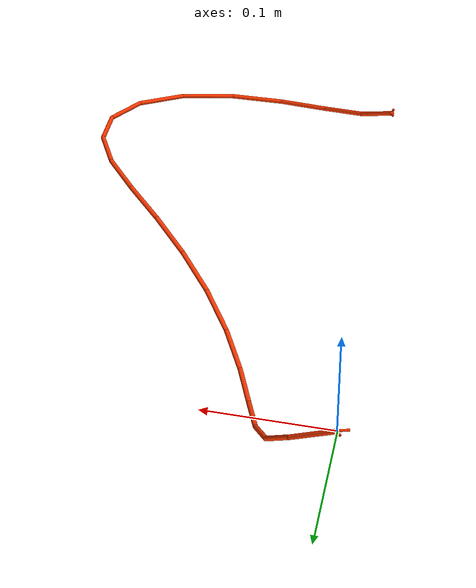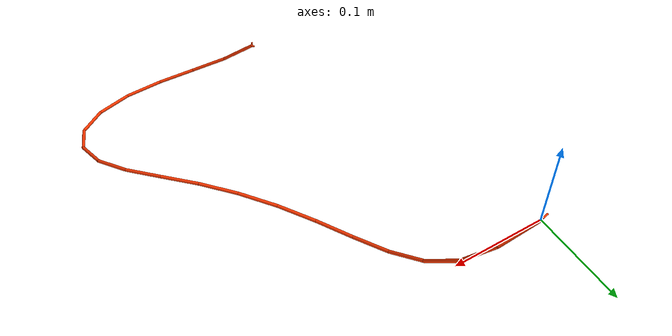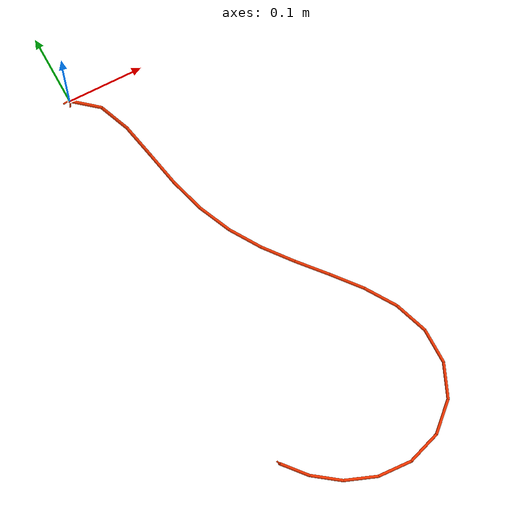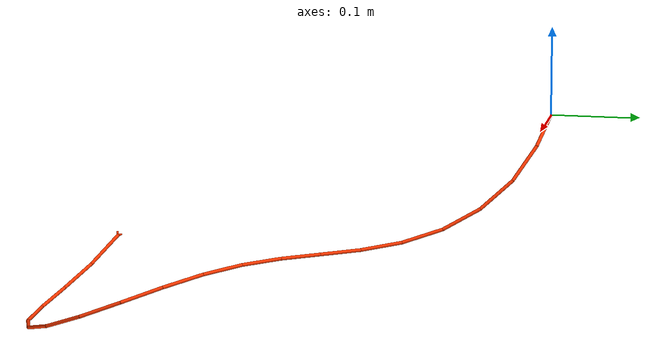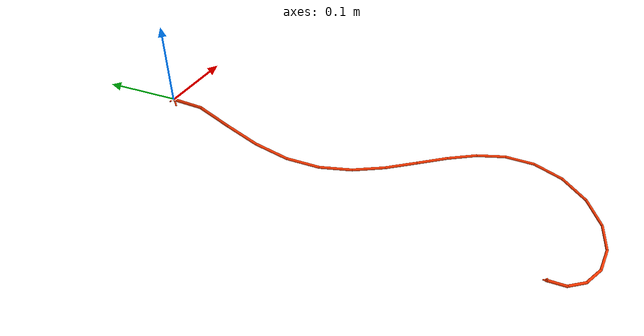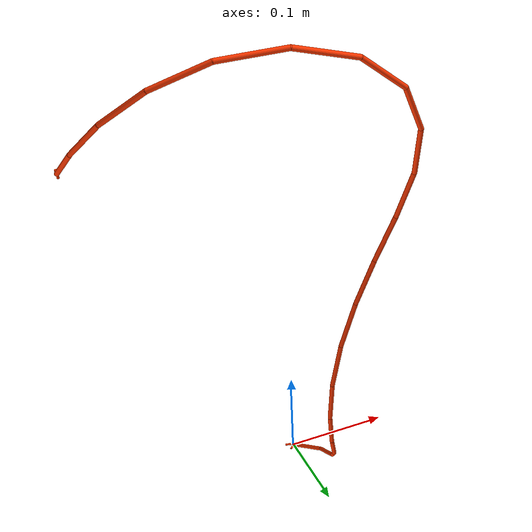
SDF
<?xml version="1.0" ?>
<sdf version="1.9">
  <model name="cable">
    <link name='cable_end_0'>
      <pose>0 0 0 0 0 0</pose>
      <inertial>
        <pose>0 0 0 0 0 0</pose>
        <mass>0.0025000000000000001</mass>
        <inertia>
          <ixx>1e-03</ixx>
          <ixy>0</ixy>
          <ixz>0</ixz>
          <iyy>1e-03</iyy>
          <iyz>0</iyz>
          <izz>1e-03</izz>
        </inertia>
      </inertial>
      <collision name='base_collision'>
        <pose>0 0 0 0 0 0</pose>
        <geometry>
          <sphere>
            <radius>0.002</radius>
          </sphere>
        </geometry>
        <surface>
          <friction>
            <torsional>
              <coefficient>0.05</coefficient>
            </torsional>
            <bullet>
              <friction>0.05</friction>
              <friction2>0.05</friction2>
            </bullet>
          </friction>
        </surface>
      </collision>
      <visual name='base_vis'>
        <pose>0 0 0 0 0 0</pose>
        <geometry>
          <sphere>
            <radius>0.002</radius>
          </sphere>
        </geometry>
        <material>
          <diffuse>1 0.219999999 0 1</diffuse>
          <specular>0.5 0.5 0.5 1</specular>
          <pbr>
            <metal>
              <roughness>0.01</roughness>
              <metalness>0.01</metalness>
            </metal>
          </pbr>
        </material>
      </visual>
      <enable_wind>false</enable_wind>
    </link>
    <joint name='joint_end_0' type='ball'>
      <pose>-5.3649599999999998e-17 1.14826e-18 -0.024 -2.7755599999999997e-17 2.91434e-16 2.7755599999999997e-17</pose>
      <child>link_1</child>
      <parent>cable_end_0</parent>
      <axis>
        <xyz>1.9813201779109516e-16 -1.5504091066542707e-17 1</xyz>
        <limit>
          <lower>-inf</lower>
          <upper>inf</upper>
          <effort>inf</effort>
          <velocity>inf</velocity>
          <stiffness>100000000</stiffness>
          <dissipation>1</dissipation>
        </limit>
        <dynamics>
          <spring_reference>0</spring_reference>
          <spring_stiffness>0</spring_stiffness>
          <damping>0.2</damping>
          <friction>0</friction>
        </dynamics>
      </axis>
    </joint>
    <link name='link_1'>
      <pose>0.018011297220716371 -0.0057942285469804178 -0.014765811474526824 -3.0575675373482318 0.9053545545132351 2.9370108755526796</pose>
      <inertial>
        <pose>0 0 0 0 0 0</pose>
        <mass>0.0025000000000000001</mass>
        <inertia>
          <ixx>1e-03</ixx>
          <ixy>0</ixy>
          <ixz>0</ixz>
          <iyy>1e-03</iyy>
          <iyz>0</iyz>
          <izz>1e-03</izz>
        </inertia>
      </inertial>
      <collision name='link_1_collision'>
        <pose>0 0 0 0 0 0</pose>
        <geometry>
          <cylinder>
            <length>0.048000000000000001</length>
            <radius>0.002</radius>
          </cylinder>
        </geometry>
        <surface>
          <friction>
            <torsional>
              <coefficient>0.05</coefficient>
            </torsional>
            <bullet>
              <friction>0.05</friction>
              <friction2>0.05</friction2>
            </bullet>
          </friction>
        </surface>
      </collision>
      <visual name='link_1_vis'>
        <pose>0 0 0 0 0 0</pose>
        <geometry>
          <cylinder>
            <length>0.048000000000000001</length>
            <radius>0.002</radius>
          </cylinder>
        </geometry>
        <material>
          <diffuse>1 0.219999999 0 1</diffuse>
          <specular>0.5 0.5 0.5 1</specular>
          <pbr>
            <metal>
              <roughness>0.01</roughness>
              <metalness>0.01</metalness>
            </metal>
          </pbr>
        </material>
      </visual>
      <collision name='sphere_1_collision'>
        <pose>0 0 0.024 0 0 0</pose>
        <geometry>
          <sphere>
            <radius>0.002</radius>
          </sphere>
        </geometry>
        <surface>
          <friction>
            <torsional>
              <coefficient>0.05</coefficient>
            </torsional>
            <bullet>
              <friction>0.05</friction>
              <friction2>0.05</friction2>
            </bullet>
          </friction>
        </surface>
      </collision>
      <visual name='sphere_1_vis'>
        <pose>0 0 0.024 0 0 0</pose>
        <geometry>
          <sphere>
            <radius>0.002</radius>
          </sphere>
        </geometry>
        <material>
          <diffuse>1 0.219999999 0 1</diffuse>
          <specular>0.5 0.5 0.5 1</specular>
          <pbr>
            <metal>
              <roughness>0.01</roughness>
              <metalness>0.01</metalness>
            </metal>
          </pbr>
        </material>
      </visual>
      <enable_wind>false</enable_wind>
    </link>
    <link name='link_2'>
      <pose>0.046816906514265177 -0.023436856932304795 -0.047395111213523133 -2.7518646546689354 0.63571418325673612 2.9148505224034569</pose>
      <inertial>
        <pose>0 0 0 0 0 0</pose>
        <mass>0.0025000000000000001</mass>
        <inertia>
          <ixx>1e-03</ixx>
          <ixy>0</ixy>
          <ixz>0</ixz>
          <iyy>1e-03</iyy>
          <iyz>0</iyz>
          <izz>1e-03</izz>
        </inertia>
      </inertial>
      <collision name='link_2_collision'>
        <pose>0 0 0 0 0 0</pose>
        <geometry>
          <cylinder>
            <length>0.048000000000000001</length>
            <radius>0.002</radius>
          </cylinder>
        </geometry>
        <surface>
          <friction>
            <torsional>
              <coefficient>0.05</coefficient>
            </torsional>
            <bullet>
              <friction>0.05</friction>
              <friction2>0.05</friction2>
            </bullet>
          </friction>
        </surface>
      </collision>
      <visual name='link_2_vis'>
        <pose>0 0 0 0 0 0</pose>
        <geometry>
          <cylinder>
            <length>0.048000000000000001</length>
            <radius>0.002</radius>
          </cylinder>
        </geometry>
        <material>
          <diffuse>1 0.219999999 0 1</diffuse>
          <specular>0.5 0.5 0.5 1</specular>
          <pbr>
            <metal>
              <roughness>0.01</roughness>
              <metalness>0.01</metalness>
            </metal>
          </pbr>
        </material>
      </visual>
      <collision name='sphere_2_collision'>
        <pose>0 0 0.024 0 0 0</pose>
        <geometry>
          <sphere>
            <radius>0.002</radius>
          </sphere>
        </geometry>
        <surface>
          <friction>
            <torsional>
              <coefficient>0.05</coefficient>
            </torsional>
            <bullet>
              <friction>0.05</friction>
              <friction2>0.05</friction2>
            </bullet>
          </friction>
        </surface>
      </collision>
      <visual name='sphere_2_vis'>
        <pose>0 0 0.024 0 0 0</pose>
        <geometry>
          <sphere>
            <radius>0.002</radius>
          </sphere>
        </geometry>
        <material>
          <diffuse>1 0.219999999 0 1</diffuse>
          <specular>0.5 0.5 0.5 1</specular>
          <pbr>
            <metal>
              <roughness>0.01</roughness>
              <metalness>0.01</metalness>
            </metal>
          </pbr>
        </material>
      </visual>
      <enable_wind>false</enable_wind>
    </link>
    <link name='link_3'>
      <pose>0.064839830329701531 -0.052318121024744868 -0.080543780538508969 -2.4469960538315578 0.59362553639905069 2.9516727700529999</pose>
      <inertial>
        <pose>0 0 0 0 0 0</pose>
        <mass>0.0025000000000000001</mass>
        <inertia>
          <ixx>1e-03</ixx>
          <ixy>0</ixy>
          <ixz>0</ixz>
          <iyy>1e-03</iyy>
          <iyz>0</iyz>
          <izz>1e-03</izz>
        </inertia>
      </inertial>
      <collision name='link_3_collision'>
        <pose>0 0 0 0 0 0</pose>
        <geometry>
          <cylinder>
            <length>0.048000000000000001</length>
            <radius>0.002</radius>
          </cylinder>
        </geometry>
        <surface>
          <friction>
            <torsional>
              <coefficient>0.05</coefficient>
            </torsional>
            <bullet>
              <friction>0.05</friction>
              <friction2>0.05</friction2>
            </bullet>
          </friction>
        </surface>
      </collision>
      <visual name='link_3_vis'>
        <pose>0 0 0 0 0 0</pose>
        <geometry>
          <cylinder>
            <length>0.048000000000000001</length>
            <radius>0.002</radius>
          </cylinder>
        </geometry>
        <material>
          <diffuse>1 0.219999999 0 1</diffuse>
          <specular>0.5 0.5 0.5 1</specular>
          <pbr>
            <metal>
              <roughness>0.01</roughness>
              <metalness>0.01</metalness>
            </metal>
          </pbr>
        </material>
      </visual>
      <collision name='sphere_3_collision'>
        <pose>0 0 0.024 0 0 0</pose>
        <geometry>
          <sphere>
            <radius>0.002</radius>
          </sphere>
        </geometry>
        <surface>
          <friction>
            <torsional>
              <coefficient>0.05</coefficient>
            </torsional>
            <bullet>
              <friction>0.05</friction>
              <friction2>0.05</friction2>
            </bullet>
          </friction>
        </surface>
      </collision>
      <visual name='sphere_3_vis'>
        <pose>0 0 0.024 0 0 0</pose>
        <geometry>
          <sphere>
            <radius>0.002</radius>
          </sphere>
        </geometry>
        <material>
          <diffuse>1 0.219999999 0 1</diffuse>
          <specular>0.5 0.5 0.5 1</specular>
          <pbr>
            <metal>
              <roughness>0.01</roughness>
              <metalness>0.01</metalness>
            </metal>
          </pbr>
        </material>
      </visual>
      <enable_wind>false</enable_wind>
    </link>
    <link name='link_4'>
      <pose>0.078607260458225969 -0.089569470643888871 -0.10698500017129564 -2.1760413321433694 0.6146191516160624 3.0747563637709492</pose>
      <inertial>
        <pose>0 0 0 0 0 0</pose>
        <mass>0.0025000000000000001</mass>
        <inertia>
          <ixx>1e-03</ixx>
          <ixy>0</ixy>
          <ixz>0</ixz>
          <iyy>1e-03</iyy>
          <iyz>0</iyz>
          <izz>1e-03</izz>
        </inertia>
      </inertial>
      <collision name='link_4_collision'>
        <pose>0 0 0 0 0 0</pose>
        <geometry>
          <cylinder>
            <length>0.048000000000000001</length>
            <radius>0.002</radius>
          </cylinder>
        </geometry>
        <surface>
          <friction>
            <torsional>
              <coefficient>0.05</coefficient>
            </torsional>
            <bullet>
              <friction>0.05</friction>
              <friction2>0.05</friction2>
            </bullet>
          </friction>
        </surface>
      </collision>
      <visual name='link_4_vis'>
        <pose>0 0 0 0 0 0</pose>
        <geometry>
          <cylinder>
            <length>0.048000000000000001</length>
            <radius>0.002</radius>
          </cylinder>
        </geometry>
        <material>
          <diffuse>1 0.219999999 0 1</diffuse>
          <specular>0.5 0.5 0.5 1</specular>
          <pbr>
            <metal>
              <roughness>0.01</roughness>
              <metalness>0.01</metalness>
            </metal>
          </pbr>
        </material>
      </visual>
      <collision name='sphere_4_collision'>
        <pose>0 0 0.024 0 0 0</pose>
        <geometry>
          <sphere>
            <radius>0.002</radius>
          </sphere>
        </geometry>
        <surface>
          <friction>
            <torsional>
              <coefficient>0.05</coefficient>
            </torsional>
            <bullet>
              <friction>0.05</friction>
              <friction2>0.05</friction2>
            </bullet>
          </friction>
        </surface>
      </collision>
      <visual name='sphere_4_vis'>
        <pose>0 0 0.024 0 0 0</pose>
        <geometry>
          <sphere>
            <radius>0.002</radius>
          </sphere>
        </geometry>
        <material>
          <diffuse>1 0.219999999 0 1</diffuse>
          <specular>0.5 0.5 0.5 1</specular>
          <pbr>
            <metal>
              <roughness>0.01</roughness>
              <metalness>0.01</metalness>
            </metal>
          </pbr>
        </material>
      </visual>
      <enable_wind>false</enable_wind>
    </link>
    <link name='link_5'>
      <pose>0.092953116278352788 -0.13148722059424489 -0.12479035499352398 -1.9154658920656293 0.60949909597980267 -2.9989073429072302</pose>
      <inertial>
        <pose>0 0 0 0 0 0</pose>
        <mass>0.0025000000000000001</mass>
        <inertia>
          <ixx>1e-03</ixx>
          <ixy>0</ixy>
          <ixz>0</ixz>
          <iyy>1e-03</iyy>
          <iyz>0</iyz>
          <izz>1e-03</izz>
        </inertia>
      </inertial>
      <collision name='link_5_collision'>
        <pose>0 0 0 0 0 0</pose>
        <geometry>
          <cylinder>
            <length>0.048000000000000001</length>
            <radius>0.002</radius>
          </cylinder>
        </geometry>
        <surface>
          <friction>
            <torsional>
              <coefficient>0.05</coefficient>
            </torsional>
            <bullet>
              <friction>0.05</friction>
              <friction2>0.05</friction2>
            </bullet>
          </friction>
        </surface>
      </collision>
      <visual name='link_5_vis'>
        <pose>0 0 0 0 0 0</pose>
        <geometry>
          <cylinder>
            <length>0.048000000000000001</length>
            <radius>0.002</radius>
          </cylinder>
        </geometry>
        <material>
          <diffuse>1 0.219999999 0 1</diffuse>
          <specular>0.5 0.5 0.5 1</specular>
          <pbr>
            <metal>
              <roughness>0.01</roughness>
              <metalness>0.01</metalness>
            </metal>
          </pbr>
        </material>
      </visual>
      <collision name='sphere_5_collision'>
        <pose>0 0 0.024 0 0 0</pose>
        <geometry>
          <sphere>
            <radius>0.002</radius>
          </sphere>
        </geometry>
        <surface>
          <friction>
            <torsional>
              <coefficient>0.05</coefficient>
            </torsional>
            <bullet>
              <friction>0.05</friction>
              <friction2>0.05</friction2>
            </bullet>
          </friction>
        </surface>
      </collision>
      <visual name='sphere_5_vis'>
        <pose>0 0 0.024 0 0 0</pose>
        <geometry>
          <sphere>
            <radius>0.002</radius>
          </sphere>
        </geometry>
        <material>
          <diffuse>1 0.219999999 0 1</diffuse>
          <specular>0.5 0.5 0.5 1</specular>
          <pbr>
            <metal>
              <roughness>0.01</roughness>
              <metalness>0.01</metalness>
            </metal>
          </pbr>
        </material>
      </visual>
      <enable_wind>false</enable_wind>
    </link>
    <link name='link_6'>
      <pose>0.11081607471797772 -0.17479171905512481 -0.13428292428795818 -1.7079619489525817 0.52317727845093753 -2.774817732811059</pose>
      <inertial>
        <pose>0 0 0 0 0 0</pose>
        <mass>0.0025000000000000001</mass>
        <inertia>
          <ixx>1e-03</ixx>
          <ixy>0</ixy>
          <ixz>0</ixz>
          <iyy>1e-03</iyy>
          <iyz>0</iyz>
          <izz>1e-03</izz>
        </inertia>
      </inertial>
      <collision name='link_6_collision'>
        <pose>0 0 0 0 0 0</pose>
        <geometry>
          <cylinder>
            <length>0.048000000000000001</length>
            <radius>0.002</radius>
          </cylinder>
        </geometry>
        <surface>
          <friction>
            <torsional>
              <coefficient>0.05</coefficient>
            </torsional>
            <bullet>
              <friction>0.05</friction>
              <friction2>0.05</friction2>
            </bullet>
          </friction>
        </surface>
      </collision>
      <visual name='link_6_vis'>
        <pose>0 0 0 0 0 0</pose>
        <geometry>
          <cylinder>
            <length>0.048000000000000001</length>
            <radius>0.002</radius>
          </cylinder>
        </geometry>
        <material>
          <diffuse>1 0.219999999 0 1</diffuse>
          <specular>0.5 0.5 0.5 1</specular>
          <pbr>
            <metal>
              <roughness>0.01</roughness>
              <metalness>0.01</metalness>
            </metal>
          </pbr>
        </material>
      </visual>
      <collision name='sphere_6_collision'>
        <pose>0 0 0.024 0 0 0</pose>
        <geometry>
          <sphere>
            <radius>0.002</radius>
          </sphere>
        </geometry>
        <surface>
          <friction>
            <torsional>
              <coefficient>0.05</coefficient>
            </torsional>
            <bullet>
              <friction>0.05</friction>
              <friction2>0.05</friction2>
            </bullet>
          </friction>
        </surface>
      </collision>
      <visual name='sphere_6_vis'>
        <pose>0 0 0.024 0 0 0</pose>
        <geometry>
          <sphere>
            <radius>0.002</radius>
          </sphere>
        </geometry>
        <material>
          <diffuse>1 0.219999999 0 1</diffuse>
          <specular>0.5 0.5 0.5 1</specular>
          <pbr>
            <metal>
              <roughness>0.01</roughness>
              <metalness>0.01</metalness>
            </metal>
          </pbr>
        </material>
      </visual>
      <enable_wind>false</enable_wind>
    </link>
    <link name='link_7'>
      <pose>0.13336436648633854 -0.21688543302341257 -0.13757353528158389 -1.5907387070594616 0.35966375676497375 -2.6010719808738831</pose>
      <inertial>
        <pose>0 0 0 0 0 0</pose>
        <mass>0.0025000000000000001</mass>
        <inertia>
          <ixx>1e-03</ixx>
          <ixy>0</ixy>
          <ixz>0</ixz>
          <iyy>1e-03</iyy>
          <iyz>0</iyz>
          <izz>1e-03</izz>
        </inertia>
      </inertial>
      <collision name='link_7_collision'>
        <pose>0 0 0 0 0 0</pose>
        <geometry>
          <cylinder>
            <length>0.048000000000000001</length>
            <radius>0.002</radius>
          </cylinder>
        </geometry>
        <surface>
          <friction>
            <torsional>
              <coefficient>0.05</coefficient>
            </torsional>
            <bullet>
              <friction>0.05</friction>
              <friction2>0.05</friction2>
            </bullet>
          </friction>
        </surface>
      </collision>
      <visual name='link_7_vis'>
        <pose>0 0 0 0 0 0</pose>
        <geometry>
          <cylinder>
            <length>0.048000000000000001</length>
            <radius>0.002</radius>
          </cylinder>
        </geometry>
        <material>
          <diffuse>1 0.219999999 0 1</diffuse>
          <specular>0.5 0.5 0.5 1</specular>
          <pbr>
            <metal>
              <roughness>0.01</roughness>
              <metalness>0.01</metalness>
            </metal>
          </pbr>
        </material>
      </visual>
      <collision name='sphere_7_collision'>
        <pose>0 0 0.024 0 0 0</pose>
        <geometry>
          <sphere>
            <radius>0.002</radius>
          </sphere>
        </geometry>
        <surface>
          <friction>
            <torsional>
              <coefficient>0.05</coefficient>
            </torsional>
            <bullet>
              <friction>0.05</friction>
              <friction2>0.05</friction2>
            </bullet>
          </friction>
        </surface>
      </collision>
      <visual name='sphere_7_vis'>
        <pose>0 0 0.024 0 0 0</pose>
        <geometry>
          <sphere>
            <radius>0.002</radius>
          </sphere>
        </geometry>
        <material>
          <diffuse>1 0.219999999 0 1</diffuse>
          <specular>0.5 0.5 0.5 1</specular>
          <pbr>
            <metal>
              <roughness>0.01</roughness>
              <metalness>0.01</metalness>
            </metal>
          </pbr>
        </material>
      </visual>
      <enable_wind>false</enable_wind>
    </link>
    <link name='link_8'>
      <pose>0.16027668432752296 -0.25655763514022878 -0.13781286443578178 -1.5620096592367017 0.15476514359934901 -2.4956541396269718</pose>
      <inertial>
        <pose>0 0 0 0 0 0</pose>
        <mass>0.0025000000000000001</mass>
        <inertia>
          <ixx>1e-03</ixx>
          <ixy>0</ixy>
          <ixz>0</ixz>
          <iyy>1e-03</iyy>
          <iyz>0</iyz>
          <izz>1e-03</izz>
        </inertia>
      </inertial>
      <collision name='link_8_collision'>
        <pose>0 0 0 0 0 0</pose>
        <geometry>
          <cylinder>
            <length>0.048000000000000001</length>
            <radius>0.002</radius>
          </cylinder>
        </geometry>
        <surface>
          <friction>
            <torsional>
              <coefficient>0.05</coefficient>
            </torsional>
            <bullet>
              <friction>0.05</friction>
              <friction2>0.05</friction2>
            </bullet>
          </friction>
        </surface>
      </collision>
      <visual name='link_8_vis'>
        <pose>0 0 0 0 0 0</pose>
        <geometry>
          <cylinder>
            <length>0.048000000000000001</length>
            <radius>0.002</radius>
          </cylinder>
        </geometry>
        <material>
          <diffuse>1 0.219999999 0 1</diffuse>
          <specular>0.5 0.5 0.5 1</specular>
          <pbr>
            <metal>
              <roughness>0.01</roughness>
              <metalness>0.01</metalness>
            </metal>
          </pbr>
        </material>
      </visual>
      <collision name='sphere_8_collision'>
        <pose>0 0 0.024 0 0 0</pose>
        <geometry>
          <sphere>
            <radius>0.002</radius>
          </sphere>
        </geometry>
        <surface>
          <friction>
            <torsional>
              <coefficient>0.05</coefficient>
            </torsional>
            <bullet>
              <friction>0.05</friction>
              <friction2>0.05</friction2>
            </bullet>
          </friction>
        </surface>
      </collision>
      <visual name='sphere_8_vis'>
        <pose>0 0 0.024 0 0 0</pose>
        <geometry>
          <sphere>
            <radius>0.002</radius>
          </sphere>
        </geometry>
        <material>
          <diffuse>1 0.219999999 0 1</diffuse>
          <specular>0.5 0.5 0.5 1</specular>
          <pbr>
            <metal>
              <roughness>0.01</roughness>
              <metalness>0.01</metalness>
            </metal>
          </pbr>
        </material>
      </visual>
      <enable_wind>false</enable_wind>
    </link>
    <link name='link_9'>
      <pose>0.1901354704094107 -0.29410788206150434 -0.13821851936839435 -1.596424648388663 -0.054273650032963694 -2.4412013003814401</pose>
      <inertial>
        <pose>0 0 0 0 0 0</pose>
        <mass>0.0025000000000000001</mass>
        <inertia>
          <ixx>1e-03</ixx>
          <ixy>0</ixy>
          <ixz>0</ixz>
          <iyy>1e-03</iyy>
          <iyz>0</iyz>
          <izz>1e-03</izz>
        </inertia>
      </inertial>
      <collision name='link_9_collision'>
        <pose>0 0 0 0 0 0</pose>
        <geometry>
          <cylinder>
            <length>0.048000000000000001</length>
            <radius>0.002</radius>
          </cylinder>
        </geometry>
        <surface>
          <friction>
            <torsional>
              <coefficient>0.05</coefficient>
            </torsional>
            <bullet>
              <friction>0.05</friction>
              <friction2>0.05</friction2>
            </bullet>
          </friction>
        </surface>
      </collision>
      <visual name='link_9_vis'>
        <pose>0 0 0 0 0 0</pose>
        <geometry>
          <cylinder>
            <length>0.048000000000000001</length>
            <radius>0.002</radius>
          </cylinder>
        </geometry>
        <material>
          <diffuse>1 0.219999999 0 1</diffuse>
          <specular>0.5 0.5 0.5 1</specular>
          <pbr>
            <metal>
              <roughness>0.01</roughness>
              <metalness>0.01</metalness>
            </metal>
          </pbr>
        </material>
      </visual>
      <collision name='sphere_9_collision'>
        <pose>0 0 0.024 0 0 0</pose>
        <geometry>
          <sphere>
            <radius>0.002</radius>
          </sphere>
        </geometry>
        <surface>
          <friction>
            <torsional>
              <coefficient>0.05</coefficient>
            </torsional>
            <bullet>
              <friction>0.05</friction>
              <friction2>0.05</friction2>
            </bullet>
          </friction>
        </surface>
      </collision>
      <visual name='sphere_9_vis'>
        <pose>0 0 0.024 0 0 0</pose>
        <geometry>
          <sphere>
            <radius>0.002</radius>
          </sphere>
        </geometry>
        <material>
          <diffuse>1 0.219999999 0 1</diffuse>
          <specular>0.5 0.5 0.5 1</specular>
          <pbr>
            <metal>
              <roughness>0.01</roughness>
              <metalness>0.01</metalness>
            </metal>
          </pbr>
        </material>
      </visual>
      <enable_wind>false</enable_wind>
    </link>
    <link name='link_10'>
      <pose>0.22107382541213005 -0.33063845050187907 -0.14123690386099708 -1.6741882695096686 -0.24432652503036914 -2.4100581216908199</pose>
      <inertial>
        <pose>0 0 0 0 0 0</pose>
        <mass>0.0025000000000000001</mass>
        <inertia>
          <ixx>1e-03</ixx>
          <ixy>0</ixy>
          <ixz>0</ixz>
          <iyy>1e-03</iyy>
          <iyz>0</iyz>
          <izz>1e-03</izz>
        </inertia>
      </inertial>
      <collision name='link_10_collision'>
        <pose>0 0 0 0 0 0</pose>
        <geometry>
          <cylinder>
            <length>0.048000000000000001</length>
            <radius>0.002</radius>
          </cylinder>
        </geometry>
        <surface>
          <friction>
            <torsional>
              <coefficient>0.05</coefficient>
            </torsional>
            <bullet>
              <friction>0.05</friction>
              <friction2>0.05</friction2>
            </bullet>
          </friction>
        </surface>
      </collision>
      <visual name='link_10_vis'>
        <pose>0 0 0 0 0 0</pose>
        <geometry>
          <cylinder>
            <length>0.048000000000000001</length>
            <radius>0.002</radius>
          </cylinder>
        </geometry>
        <material>
          <diffuse>1 0.219999999 0 1</diffuse>
          <specular>0.5 0.5 0.5 1</specular>
          <pbr>
            <metal>
              <roughness>0.01</roughness>
              <metalness>0.01</metalness>
            </metal>
          </pbr>
        </material>
      </visual>
      <collision name='sphere_10_collision'>
        <pose>0 0 0.024 0 0 0</pose>
        <geometry>
          <sphere>
            <radius>0.002</radius>
          </sphere>
        </geometry>
        <surface>
          <friction>
            <torsional>
              <coefficient>0.05</coefficient>
            </torsional>
            <bullet>
              <friction>0.05</friction>
              <friction2>0.05</friction2>
            </bullet>
          </friction>
        </surface>
      </collision>
      <visual name='sphere_10_vis'>
        <pose>0 0 0.024 0 0 0</pose>
        <geometry>
          <sphere>
            <radius>0.002</radius>
          </sphere>
        </geometry>
        <material>
          <diffuse>1 0.219999999 0 1</diffuse>
          <specular>0.5 0.5 0.5 1</specular>
          <pbr>
            <metal>
              <roughness>0.01</roughness>
              <metalness>0.01</metalness>
            </metal>
          </pbr>
        </material>
      </visual>
      <enable_wind>false</enable_wind>
    </link>
    <link name='link_11'>
      <pose>0.25035724821834471 -0.36788545594327826 -0.14832498184318643 -1.787556454728058 -0.43324175328408771 -2.4238720880978213</pose>
      <inertial>
        <pose>0 0 0 0 0 0</pose>
        <mass>0.0025000000000000001</mass>
        <inertia>
          <ixx>1e-03</ixx>
          <ixy>0</ixy>
          <ixz>0</ixz>
          <iyy>1e-03</iyy>
          <iyz>0</iyz>
          <izz>1e-03</izz>
        </inertia>
      </inertial>
      <collision name='link_11_collision'>
        <pose>0 0 0 0 0 0</pose>
        <geometry>
          <cylinder>
            <length>0.048000000000000001</length>
            <radius>0.002</radius>
          </cylinder>
        </geometry>
        <surface>
          <friction>
            <torsional>
              <coefficient>0.05</coefficient>
            </torsional>
            <bullet>
              <friction>0.05</friction>
              <friction2>0.05</friction2>
            </bullet>
          </friction>
        </surface>
      </collision>
      <visual name='link_11_vis'>
        <pose>0 0 0 0 0 0</pose>
        <geometry>
          <cylinder>
            <length>0.048000000000000001</length>
            <radius>0.002</radius>
          </cylinder>
        </geometry>
        <material>
          <diffuse>1 0.219999999 0 1</diffuse>
          <specular>0.5 0.5 0.5 1</specular>
          <pbr>
            <metal>
              <roughness>0.01</roughness>
              <metalness>0.01</metalness>
            </metal>
          </pbr>
        </material>
      </visual>
      <collision name='sphere_11_collision'>
        <pose>0 0 0.024 0 0 0</pose>
        <geometry>
          <sphere>
            <radius>0.002</radius>
          </sphere>
        </geometry>
        <surface>
          <friction>
            <torsional>
              <coefficient>0.05</coefficient>
            </torsional>
            <bullet>
              <friction>0.05</friction>
              <friction2>0.05</friction2>
            </bullet>
          </friction>
        </surface>
      </collision>
      <visual name='sphere_11_vis'>
        <pose>0 0 0.024 0 0 0</pose>
        <geometry>
          <sphere>
            <radius>0.002</radius>
          </sphere>
        </geometry>
        <material>
          <diffuse>1 0.219999999 0 1</diffuse>
          <specular>0.5 0.5 0.5 1</specular>
          <pbr>
            <metal>
              <roughness>0.01</roughness>
              <metalness>0.01</metalness>
            </metal>
          </pbr>
        </material>
      </visual>
      <enable_wind>false</enable_wind>
    </link>
    <link name='link_12'>
      <pose>0.2734095469215152 -0.40798340836926178 -0.15997015399377268 -1.9303203301589287 -0.60183305263011 -2.5165214897159043</pose>
      <inertial>
        <pose>0 0 0 0 0 0</pose>
        <mass>0.0025000000000000001</mass>
        <inertia>
          <ixx>1e-03</ixx>
          <ixy>0</ixy>
          <ixz>0</ixz>
          <iyy>1e-03</iyy>
          <iyz>0</iyz>
          <izz>1e-03</izz>
        </inertia>
      </inertial>
      <collision name='link_12_collision'>
        <pose>0 0 0 0 0 0</pose>
        <geometry>
          <cylinder>
            <length>0.048000000000000001</length>
            <radius>0.002</radius>
          </cylinder>
        </geometry>
        <surface>
          <friction>
            <torsional>
              <coefficient>0.05</coefficient>
            </torsional>
            <bullet>
              <friction>0.05</friction>
              <friction2>0.05</friction2>
            </bullet>
          </friction>
        </surface>
      </collision>
      <visual name='link_12_vis'>
        <pose>0 0 0 0 0 0</pose>
        <geometry>
          <cylinder>
            <length>0.048000000000000001</length>
            <radius>0.002</radius>
          </cylinder>
        </geometry>
        <material>
          <diffuse>1 0.219999999 0 1</diffuse>
          <specular>0.5 0.5 0.5 1</specular>
          <pbr>
            <metal>
              <roughness>0.01</roughness>
              <metalness>0.01</metalness>
            </metal>
          </pbr>
        </material>
      </visual>
      <collision name='sphere_12_collision'>
        <pose>0 0 0.024 0 0 0</pose>
        <geometry>
          <sphere>
            <radius>0.002</radius>
          </sphere>
        </geometry>
        <surface>
          <friction>
            <torsional>
              <coefficient>0.05</coefficient>
            </torsional>
            <bullet>
              <friction>0.05</friction>
              <friction2>0.05</friction2>
            </bullet>
          </friction>
        </surface>
      </collision>
      <visual name='sphere_12_vis'>
        <pose>0 0 0.024 0 0 0</pose>
        <geometry>
          <sphere>
            <radius>0.002</radius>
          </sphere>
        </geometry>
        <material>
          <diffuse>1 0.219999999 0 1</diffuse>
          <specular>0.5 0.5 0.5 1</specular>
          <pbr>
            <metal>
              <roughness>0.01</roughness>
              <metalness>0.01</metalness>
            </metal>
          </pbr>
        </material>
      </visual>
      <enable_wind>false</enable_wind>
    </link>
    <link name='link_13'>
      <pose>0.28437702991563274 -0.45137978538792922 -0.17542906697939153 -2.0821926807433639 -0.7618271666957821 -2.6962624797604873</pose>
      <inertial>
        <pose>0 0 0 0 0 0</pose>
        <mass>0.0025000000000000001</mass>
        <inertia>
          <ixx>1e-03</ixx>
          <ixy>0</ixy>
          <ixz>0</ixz>
          <iyy>1e-03</iyy>
          <iyz>0</iyz>
          <izz>1e-03</izz>
        </inertia>
      </inertial>
      <collision name='link_13_collision'>
        <pose>0 0 0 0 0 0</pose>
        <geometry>
          <cylinder>
            <length>0.048000000000000001</length>
            <radius>0.002</radius>
          </cylinder>
        </geometry>
        <surface>
          <friction>
            <torsional>
              <coefficient>0.05</coefficient>
            </torsional>
            <bullet>
              <friction>0.05</friction>
              <friction2>0.05</friction2>
            </bullet>
          </friction>
        </surface>
      </collision>
      <visual name='link_13_vis'>
        <pose>0 0 0 0 0 0</pose>
        <geometry>
          <cylinder>
            <length>0.048000000000000001</length>
            <radius>0.002</radius>
          </cylinder>
        </geometry>
        <material>
          <diffuse>1 0.219999999 0 1</diffuse>
          <specular>0.5 0.5 0.5 1</specular>
          <pbr>
            <metal>
              <roughness>0.01</roughness>
              <metalness>0.01</metalness>
            </metal>
          </pbr>
        </material>
      </visual>
      <collision name='sphere_13_collision'>
        <pose>0 0 0.024 0 0 0</pose>
        <geometry>
          <sphere>
            <radius>0.002</radius>
          </sphere>
        </geometry>
        <surface>
          <friction>
            <torsional>
              <coefficient>0.05</coefficient>
            </torsional>
            <bullet>
              <friction>0.05</friction>
              <friction2>0.05</friction2>
            </bullet>
          </friction>
        </surface>
      </collision>
      <visual name='sphere_13_vis'>
        <pose>0 0 0.024 0 0 0</pose>
        <geometry>
          <sphere>
            <radius>0.002</radius>
          </sphere>
        </geometry>
        <material>
          <diffuse>1 0.219999999 0 1</diffuse>
          <specular>0.5 0.5 0.5 1</specular>
          <pbr>
            <metal>
              <roughness>0.01</roughness>
              <metalness>0.01</metalness>
            </metal>
          </pbr>
        </material>
      </visual>
      <enable_wind>false</enable_wind>
    </link>
    <link name='link_14'>
      <pose>0.27803972098989993 -0.49473782711713066 -0.19237713837956083 -2.1959020701493697 -0.9252885836841821 -2.9845158248824699</pose>
      <inertial>
        <pose>0 0 0 0 0 0</pose>
        <mass>0.0025000000000000001</mass>
        <inertia>
          <ixx>1e-03</ixx>
          <ixy>0</ixy>
          <ixz>0</ixz>
          <iyy>1e-03</iyy>
          <iyz>0</iyz>
          <izz>1e-03</izz>
        </inertia>
      </inertial>
      <collision name='link_14_collision'>
        <pose>0 0 0 0 0 0</pose>
        <geometry>
          <cylinder>
            <length>0.048000000000000001</length>
            <radius>0.002</radius>
          </cylinder>
        </geometry>
        <surface>
          <friction>
            <torsional>
              <coefficient>0.05</coefficient>
            </torsional>
            <bullet>
              <friction>0.05</friction>
              <friction2>0.05</friction2>
            </bullet>
          </friction>
        </surface>
      </collision>
      <visual name='link_14_vis'>
        <pose>0 0 0 0 0 0</pose>
        <geometry>
          <cylinder>
            <length>0.048000000000000001</length>
            <radius>0.002</radius>
          </cylinder>
        </geometry>
        <material>
          <diffuse>1 0.219999999 0 1</diffuse>
          <specular>0.5 0.5 0.5 1</specular>
          <pbr>
            <metal>
              <roughness>0.01</roughness>
              <metalness>0.01</metalness>
            </metal>
          </pbr>
        </material>
      </visual>
      <collision name='sphere_14_collision'>
        <pose>0 0 0.024 0 0 0</pose>
        <geometry>
          <sphere>
            <radius>0.002</radius>
          </sphere>
        </geometry>
        <surface>
          <friction>
            <torsional>
              <coefficient>0.05</coefficient>
            </torsional>
            <bullet>
              <friction>0.05</friction>
              <friction2>0.05</friction2>
            </bullet>
          </friction>
        </surface>
      </collision>
      <visual name='sphere_14_vis'>
        <pose>0 0 0.024 0 0 0</pose>
        <geometry>
          <sphere>
            <radius>0.002</radius>
          </sphere>
        </geometry>
        <material>
          <diffuse>1 0.219999999 0 1</diffuse>
          <specular>0.5 0.5 0.5 1</specular>
          <pbr>
            <metal>
              <roughness>0.01</roughness>
              <metalness>0.01</metalness>
            </metal>
          </pbr>
        </material>
      </visual>
      <enable_wind>false</enable_wind>
    </link>
    <link name='link_15'>
      <pose>0.25279087720374438 -0.53122815446106442 -0.20707835760586291 -2.1606090637664961 -1.0833264152950239 2.8383501633092383</pose>
      <inertial>
        <pose>0 0 0 0 0 0</pose>
        <mass>0.0025000000000000001</mass>
        <inertia>
          <ixx>1e-03</ixx>
          <ixy>0</ixy>
          <ixz>0</ixz>
          <iyy>1e-03</iyy>
          <iyz>0</iyz>
          <izz>1e-03</izz>
        </inertia>
      </inertial>
      <collision name='link_15_collision'>
        <pose>0 0 0 0 0 0</pose>
        <geometry>
          <cylinder>
            <length>0.048000000000000001</length>
            <radius>0.002</radius>
          </cylinder>
        </geometry>
        <surface>
          <friction>
            <torsional>
              <coefficient>0.05</coefficient>
            </torsional>
            <bullet>
              <friction>0.05</friction>
              <friction2>0.05</friction2>
            </bullet>
          </friction>
        </surface>
      </collision>
      <visual name='link_15_vis'>
        <pose>0 0 0 0 0 0</pose>
        <geometry>
          <cylinder>
            <length>0.048000000000000001</length>
            <radius>0.002</radius>
          </cylinder>
        </geometry>
        <material>
          <diffuse>1 0.219999999 0 1</diffuse>
          <specular>0.5 0.5 0.5 1</specular>
          <pbr>
            <metal>
              <roughness>0.01</roughness>
              <metalness>0.01</metalness>
            </metal>
          </pbr>
        </material>
      </visual>
      <collision name='sphere_15_collision'>
        <pose>0 0 0.024 0 0 0</pose>
        <geometry>
          <sphere>
            <radius>0.002</radius>
          </sphere>
        </geometry>
        <surface>
          <friction>
            <torsional>
              <coefficient>0.05</coefficient>
            </torsional>
            <bullet>
              <friction>0.05</friction>
              <friction2>0.05</friction2>
            </bullet>
          </friction>
        </surface>
      </collision>
      <visual name='sphere_15_vis'>
        <pose>0 0 0.024 0 0 0</pose>
        <geometry>
          <sphere>
            <radius>0.002</radius>
          </sphere>
        </geometry>
        <material>
          <diffuse>1 0.219999999 0 1</diffuse>
          <specular>0.5 0.5 0.5 1</specular>
          <pbr>
            <metal>
              <roughness>0.01</roughness>
              <metalness>0.01</metalness>
            </metal>
          </pbr>
        </material>
      </visual>
      <enable_wind>false</enable_wind>
    </link>
    <link name='link_16'>
      <pose>0.2128231608085922 -0.553957691333263 -0.21581172850132968 -1.8387614947747495 -1.1697121753885023 2.1254354565196074</pose>
      <inertial>
        <pose>0 0 0 0 0 0</pose>
        <mass>0.0025000000000000001</mass>
        <inertia>
          <ixx>1e-03</ixx>
          <ixy>0</ixy>
          <ixz>0</ixz>
          <iyy>1e-03</iyy>
          <iyz>0</iyz>
          <izz>1e-03</izz>
        </inertia>
      </inertial>
      <collision name='link_16_collision'>
        <pose>0 0 0 0 0 0</pose>
        <geometry>
          <cylinder>
            <length>0.048000000000000001</length>
            <radius>0.002</radius>
          </cylinder>
        </geometry>
        <surface>
          <friction>
            <torsional>
              <coefficient>0.05</coefficient>
            </torsional>
            <bullet>
              <friction>0.05</friction>
              <friction2>0.05</friction2>
            </bullet>
          </friction>
        </surface>
      </collision>
      <visual name='link_16_vis'>
        <pose>0 0 0 0 0 0</pose>
        <geometry>
          <cylinder>
            <length>0.048000000000000001</length>
            <radius>0.002</radius>
          </cylinder>
        </geometry>
        <material>
          <diffuse>1 0.219999999 0 1</diffuse>
          <specular>0.5 0.5 0.5 1</specular>
          <pbr>
            <metal>
              <roughness>0.01</roughness>
              <metalness>0.01</metalness>
            </metal>
          </pbr>
        </material>
      </visual>
      <collision name='sphere_16_collision'>
        <pose>0 0 0.024 0 0 0</pose>
        <geometry>
          <sphere>
            <radius>0.002</radius>
          </sphere>
        </geometry>
        <surface>
          <friction>
            <torsional>
              <coefficient>0.05</coefficient>
            </torsional>
            <bullet>
              <friction>0.05</friction>
              <friction2>0.05</friction2>
            </bullet>
          </friction>
        </surface>
      </collision>
      <visual name='sphere_16_vis'>
        <pose>0 0 0.024 0 0 0</pose>
        <geometry>
          <sphere>
            <radius>0.002</radius>
          </sphere>
        </geometry>
        <material>
          <diffuse>1 0.219999999 0 1</diffuse>
          <specular>0.5 0.5 0.5 1</specular>
          <pbr>
            <metal>
              <roughness>0.01</roughness>
              <metalness>0.01</metalness>
            </metal>
          </pbr>
        </material>
      </visual>
      <enable_wind>false</enable_wind>
    </link>
    <link name='link_17'>
      <pose>0.16615093408238613 -0.56014325339729276 -0.21656687960834353 -1.4099058566066822 -1.1054260379540222 1.3837810921195202</pose>
      <inertial>
        <pose>0 0 0 0 0 0</pose>
        <mass>0.0025000000000000001</mass>
        <inertia>
          <ixx>1e-03</ixx>
          <ixy>0</ixy>
          <ixz>0</ixz>
          <iyy>1e-03</iyy>
          <iyz>0</iyz>
          <izz>1e-03</izz>
        </inertia>
      </inertial>
      <collision name='link_17_collision'>
        <pose>0 0 0 0 0 0</pose>
        <geometry>
          <cylinder>
            <length>0.048000000000000001</length>
            <radius>0.002</radius>
          </cylinder>
        </geometry>
        <surface>
          <friction>
            <torsional>
              <coefficient>0.05</coefficient>
            </torsional>
            <bullet>
              <friction>0.05</friction>
              <friction2>0.05</friction2>
            </bullet>
          </friction>
        </surface>
      </collision>
      <visual name='link_17_vis'>
        <pose>0 0 0 0 0 0</pose>
        <geometry>
          <cylinder>
            <length>0.048000000000000001</length>
            <radius>0.002</radius>
          </cylinder>
        </geometry>
        <material>
          <diffuse>1 0.219999999 0 1</diffuse>
          <specular>0.5 0.5 0.5 1</specular>
          <pbr>
            <metal>
              <roughness>0.01</roughness>
              <metalness>0.01</metalness>
            </metal>
          </pbr>
        </material>
      </visual>
      <collision name='sphere_17_collision'>
        <pose>0 0 0.024 0 0 0</pose>
        <geometry>
          <sphere>
            <radius>0.002</radius>
          </sphere>
        </geometry>
        <surface>
          <friction>
            <torsional>
              <coefficient>0.05</coefficient>
            </torsional>
            <bullet>
              <friction>0.05</friction>
              <friction2>0.05</friction2>
            </bullet>
          </friction>
        </surface>
      </collision>
      <visual name='sphere_17_vis'>
        <pose>0 0 0.024 0 0 0</pose>
        <geometry>
          <sphere>
            <radius>0.002</radius>
          </sphere>
        </geometry>
        <material>
          <diffuse>1 0.219999999 0 1</diffuse>
          <specular>0.5 0.5 0.5 1</specular>
          <pbr>
            <metal>
              <roughness>0.01</roughness>
              <metalness>0.01</metalness>
            </metal>
          </pbr>
        </material>
      </visual>
      <enable_wind>false</enable_wind>
    </link>
    <link name='link_18'>
      <pose>0.12002927049583612 -0.55209500816063095 -0.20904239642648681 -1.1489406730496314 -0.93948726610603972 0.91706618755575786</pose>
      <inertial>
        <pose>0 0 0 0 0 0</pose>
        <mass>0.0025000000000000001</mass>
        <inertia>
          <ixx>1e-03</ixx>
          <ixy>0</ixy>
          <ixz>0</ixz>
          <iyy>1e-03</iyy>
          <iyz>0</iyz>
          <izz>1e-03</izz>
        </inertia>
      </inertial>
      <collision name='link_18_collision'>
        <pose>0 0 0 0 0 0</pose>
        <geometry>
          <cylinder>
            <length>0.048000000000000001</length>
            <radius>0.002</radius>
          </cylinder>
        </geometry>
        <surface>
          <friction>
            <torsional>
              <coefficient>0.05</coefficient>
            </torsional>
            <bullet>
              <friction>0.05</friction>
              <friction2>0.05</friction2>
            </bullet>
          </friction>
        </surface>
      </collision>
      <visual name='link_18_vis'>
        <pose>0 0 0 0 0 0</pose>
        <geometry>
          <cylinder>
            <length>0.048000000000000001</length>
            <radius>0.002</radius>
          </cylinder>
        </geometry>
        <material>
          <diffuse>1 0.219999999 0 1</diffuse>
          <specular>0.5 0.5 0.5 1</specular>
          <pbr>
            <metal>
              <roughness>0.01</roughness>
              <metalness>0.01</metalness>
            </metal>
          </pbr>
        </material>
      </visual>
      <collision name='sphere_18_collision'>
        <pose>0 0 0.024 0 0 0</pose>
        <geometry>
          <sphere>
            <radius>0.002</radius>
          </sphere>
        </geometry>
        <surface>
          <friction>
            <torsional>
              <coefficient>0.05</coefficient>
            </torsional>
            <bullet>
              <friction>0.05</friction>
              <friction2>0.05</friction2>
            </bullet>
          </friction>
        </surface>
      </collision>
      <visual name='sphere_18_vis'>
        <pose>0 0 0.024 0 0 0</pose>
        <geometry>
          <sphere>
            <radius>0.002</radius>
          </sphere>
        </geometry>
        <material>
          <diffuse>1 0.219999999 0 1</diffuse>
          <specular>0.5 0.5 0.5 1</specular>
          <pbr>
            <metal>
              <roughness>0.01</roughness>
              <metalness>0.01</metalness>
            </metal>
          </pbr>
        </material>
      </visual>
      <enable_wind>false</enable_wind>
    </link>
    <link name='link_19'>
      <pose>0.078902932469800291 -0.53418812201646682 -0.19326701760381337 -0.97313522617424386 -0.73978813605993954 0.61835622775427523</pose>
      <inertial>
        <pose>0 0 0 0 0 0</pose>
        <mass>0.0025000000000000001</mass>
        <inertia>
          <ixx>1e-03</ixx>
          <ixy>0</ixy>
          <ixz>0</ixz>
          <iyy>1e-03</iyy>
          <iyz>0</iyz>
          <izz>1e-03</izz>
        </inertia>
      </inertial>
      <collision name='link_19_collision'>
        <pose>0 0 0 0 0 0</pose>
        <geometry>
          <cylinder>
            <length>0.048000000000000001</length>
            <radius>0.002</radius>
          </cylinder>
        </geometry>
        <surface>
          <friction>
            <torsional>
              <coefficient>0.05</coefficient>
            </torsional>
            <bullet>
              <friction>0.05</friction>
              <friction2>0.05</friction2>
            </bullet>
          </friction>
        </surface>
      </collision>
      <visual name='link_19_vis'>
        <pose>0 0 0 0 0 0</pose>
        <geometry>
          <cylinder>
            <length>0.048000000000000001</length>
            <radius>0.002</radius>
          </cylinder>
        </geometry>
        <material>
          <diffuse>1 0.219999999 0 1</diffuse>
          <specular>0.5 0.5 0.5 1</specular>
          <pbr>
            <metal>
              <roughness>0.01</roughness>
              <metalness>0.01</metalness>
            </metal>
          </pbr>
        </material>
      </visual>
      <collision name='sphere_19_collision'>
        <pose>0 0 0.024 0 0 0</pose>
        <geometry>
          <sphere>
            <radius>0.002</radius>
          </sphere>
        </geometry>
        <surface>
          <friction>
            <torsional>
              <coefficient>0.05</coefficient>
            </torsional>
            <bullet>
              <friction>0.05</friction>
              <friction2>0.05</friction2>
            </bullet>
          </friction>
        </surface>
      </collision>
      <visual name='sphere_19_vis'>
        <pose>0 0 0.024 0 0 0</pose>
        <geometry>
          <sphere>
            <radius>0.002</radius>
          </sphere>
        </geometry>
        <material>
          <diffuse>1 0.219999999 0 1</diffuse>
          <specular>0.5 0.5 0.5 1</specular>
          <pbr>
            <metal>
              <roughness>0.01</roughness>
              <metalness>0.01</metalness>
            </metal>
          </pbr>
        </material>
      </visual>
      <enable_wind>false</enable_wind>
    </link>
    <link name='link_20'>
      <pose>0.045028636960572133 -0.51107769861639185 -0.16904195294909163 -0.80513019872936498 -0.54194690480703012 0.42532356523412918</pose>
      <inertial>
        <pose>0 0 0 0 0 0</pose>
        <mass>0.0025000000000000001</mass>
        <inertia>
          <ixx>1e-03</ixx>
          <ixy>0</ixy>
          <ixz>0</ixz>
          <iyy>1e-03</iyy>
          <iyz>0</iyz>
          <izz>1e-03</izz>
        </inertia>
      </inertial>
      <collision name='link_20_collision'>
        <pose>0 0 0 0 0 0</pose>
        <geometry>
          <cylinder>
            <length>0.048000000000000001</length>
            <radius>0.002</radius>
          </cylinder>
        </geometry>
        <surface>
          <friction>
            <torsional>
              <coefficient>0.05</coefficient>
            </torsional>
            <bullet>
              <friction>0.05</friction>
              <friction2>0.05</friction2>
            </bullet>
          </friction>
        </surface>
      </collision>
      <visual name='link_20_vis'>
        <pose>0 0 0 0 0 0</pose>
        <geometry>
          <cylinder>
            <length>0.048000000000000001</length>
            <radius>0.002</radius>
          </cylinder>
        </geometry>
        <material>
          <diffuse>1 0.219999999 0 1</diffuse>
          <specular>0.5 0.5 0.5 1</specular>
          <pbr>
            <metal>
              <roughness>0.01</roughness>
              <metalness>0.01</metalness>
            </metal>
          </pbr>
        </material>
      </visual>
      <collision name='sphere_20_collision'>
        <pose>0 0 0.024 0 0 0</pose>
        <geometry>
          <sphere>
            <radius>0.002</radius>
          </sphere>
        </geometry>
        <surface>
          <friction>
            <torsional>
              <coefficient>0.05</coefficient>
            </torsional>
            <bullet>
              <friction>0.05</friction>
              <friction2>0.05</friction2>
            </bullet>
          </friction>
        </surface>
      </collision>
      <visual name='sphere_20_vis'>
        <pose>0 0 0.024 0 0 0</pose>
        <geometry>
          <sphere>
            <radius>0.002</radius>
          </sphere>
        </geometry>
        <material>
          <diffuse>1 0.219999999 0 1</diffuse>
          <specular>0.5 0.5 0.5 1</specular>
          <pbr>
            <metal>
              <roughness>0.01</roughness>
              <metalness>0.01</metalness>
            </metal>
          </pbr>
        </material>
      </visual>
      <enable_wind>false</enable_wind>
    </link>
    <joint name='joint_1' type='ball'>
      <pose>-6.9388900000000004e-18 1.9082000000000001e-17 -0.024 -1.34815e-33 9.7144500000000003e-17 -2.7755599999999997e-17</pose>
      <parent>link_1</parent>
      <child>link_2</child>
      <axis>
        <xyz>-2.5568197732639408e-16 -6.9388939039072308e-17 1</xyz>
        <limit>
          <lower>-inf</lower>
          <upper>inf</upper>
          <effort>inf</effort>
          <velocity>inf</velocity>
          <stiffness>100000000</stiffness>
          <dissipation>1</dissipation>
        </limit>
        <dynamics>
          <spring_reference>0</spring_reference>
          <spring_stiffness>0</spring_stiffness>
          <damping>0.2</damping>
          <friction>0</friction>
        </dynamics>
      </axis>
    </joint>
    <joint name='joint_2' type='ball'>
      <pose>-2.0122800000000001e-16 3.8163900000000001e-17 -0.024 7.7037199999999994e-34 1.3877799999999999e-17 1.11022e-16</pose>
      <parent>link_2</parent>
      <child>link_3</child>
      <axis>
        <xyz>-4.336808689942141e-19 7.63278329429795e-17 1</xyz>
        <limit>
          <lower>-inf</lower>
          <upper>inf</upper>
          <effort>inf</effort>
          <velocity>inf</velocity>
          <stiffness>100000000</stiffness>
          <dissipation>1</dissipation>
        </limit>
        <dynamics>
          <spring_reference>0</spring_reference>
          <spring_stiffness>0</spring_stiffness>
          <damping>0.2</damping>
          <friction>0</friction>
        </dynamics>
      </axis>
    </joint>
    <joint name='joint_3' type='ball'>
      <pose>-3.4347499999999998e-16 5.5511199999999995e-17 -0.024 -5.5511199999999995e-17 4.1633400000000002e-17 8.3266699999999998e-17</pose>
      <parent>link_3</parent>
      <child>link_4</child>
      <axis>
        <xyz>-1.1102230246251565e-16 1.1102230246251564e-16 1</xyz>
        <limit>
          <lower>-inf</lower>
          <upper>inf</upper>
          <effort>inf</effort>
          <velocity>inf</velocity>
          <stiffness>100000000</stiffness>
          <dissipation>1</dissipation>
        </limit>
        <dynamics>
          <spring_reference>0</spring_reference>
          <spring_stiffness>0</spring_stiffness>
          <damping>0.2</damping>
          <friction>0</friction>
        </dynamics>
      </axis>
    </joint>
    <joint name='joint_4' type='ball'>
      <pose>-3.0531099999999999e-16 -9.0205599999999994e-17 -0.024 0 6.9388900000000005e-17 0</pose>
      <parent>link_4</parent>
      <child>link_5</child>
      <axis>
        <xyz>1.3183898417423731e-16 5.5511151231257839e-17 1</xyz>
        <limit>
          <lower>-inf</lower>
          <upper>inf</upper>
          <effort>inf</effort>
          <velocity>inf</velocity>
          <stiffness>100000000</stiffness>
          <dissipation>1</dissipation>
        </limit>
        <dynamics>
          <spring_reference>0</spring_reference>
          <spring_stiffness>0</spring_stiffness>
          <damping>0.2</damping>
          <friction>0</friction>
        </dynamics>
      </axis>
    </joint>
    <joint name='joint_5' type='ball'>
      <pose>-6.7307299999999996e-16 -1.52656e-16 -0.024 5.5511199999999995e-17 -1.3877799999999999e-17 -1.6653299999999999e-16</pose>
      <parent>link_5</parent>
      <child>link_6</child>
      <axis>
        <xyz>-2.0816681711721636e-17 1.1102230246251565e-16 1</xyz>
        <limit>
          <lower>-inf</lower>
          <upper>inf</upper>
          <effort>inf</effort>
          <velocity>inf</velocity>
          <stiffness>100000000</stiffness>
          <dissipation>1</dissipation>
        </limit>
        <dynamics>
          <spring_reference>0</spring_reference>
          <spring_stiffness>0</spring_stiffness>
          <damping>0.2</damping>
          <friction>0</friction>
        </dynamics>
      </axis>
    </joint>
    <joint name='joint_6' type='ball'>
      <pose>-5.0653900000000003e-16 -2.0816700000000001e-16 -0.024 1.11022e-16 -6.2449999999999997e-17 2.77556e-16</pose>
      <parent>link_6</parent>
      <child>link_7</child>
      <axis>
        <xyz>-5.8980598183211417e-17 1.3877787807814417e-17 1</xyz>
        <limit>
          <lower>-inf</lower>
          <upper>inf</upper>
          <effort>inf</effort>
          <velocity>inf</velocity>
          <stiffness>100000000</stiffness>
          <dissipation>1</dissipation>
        </limit>
        <dynamics>
          <spring_reference>0</spring_reference>
          <spring_stiffness>0</spring_stiffness>
          <damping>0.2</damping>
          <friction>0</friction>
        </dynamics>
      </axis>
    </joint>
    <joint name='joint_7' type='ball'>
      <pose>-3.4694500000000001e-16 -1.80411e-16 -0.024 -2.2204499999999999e-16 3.67761e-16 4.9959999999999997e-16</pose>
      <parent>link_7</parent>
      <child>link_8</child>
      <axis>
        <xyz>2.2985086056692689e-16 1.960237527853792e-16 1</xyz>
        <limit>
          <lower>-inf</lower>
          <upper>inf</upper>
          <effort>inf</effort>
          <velocity>inf</velocity>
          <stiffness>100000000</stiffness>
          <dissipation>1</dissipation>
        </limit>
        <dynamics>
          <spring_reference>0</spring_reference>
          <spring_stiffness>0</spring_stiffness>
          <damping>0.2</damping>
          <friction>0</friction>
        </dynamics>
      </axis>
    </joint>
    <joint name='joint_8' type='ball'>
      <pose>-2.6367799999999999e-16 -7.4940100000000003e-16 -0.024 -1.5022300000000001e-32 -1.80411e-16 1.6653299999999999e-16</pose>
      <parent>link_8</parent>
      <child>link_9</child>
      <axis>
        <xyz>-1.5742615544489524e-16 4.163336342344337e-17 1</xyz>
        <limit>
          <lower>-inf</lower>
          <upper>inf</upper>
          <effort>inf</effort>
          <velocity>inf</velocity>
          <stiffness>100000000</stiffness>
          <dissipation>1</dissipation>
        </limit>
        <dynamics>
          <spring_reference>0</spring_reference>
          <spring_stiffness>0</spring_stiffness>
          <damping>0.2</damping>
          <friction>0</friction>
        </dynamics>
      </axis>
    </joint>
    <joint name='joint_9' type='ball'>
      <pose>2.7755599999999997e-17 -2.91434e-16 -0.024 -5.5511199999999995e-17 -2.7755599999999997e-17 -5.5511199999999995e-17</pose>
      <parent>link_9</parent>
      <child>link_10</child>
      <axis>
        <xyz>-7.2858385991025898e-17 -1.0408340855860843e-16 1</xyz>
        <limit>
          <lower>-inf</lower>
          <upper>inf</upper>
          <effort>inf</effort>
          <velocity>inf</velocity>
          <stiffness>100000000</stiffness>
          <dissipation>1</dissipation>
        </limit>
        <dynamics>
          <spring_reference>0</spring_reference>
          <spring_stiffness>0</spring_stiffness>
          <damping>0.2</damping>
          <friction>0</friction>
        </dynamics>
      </axis>
    </joint>
    <joint name='joint_10' type='ball'>
      <pose>-2.7755599999999997e-17 -4.3021100000000001e-16 -0.024 -1.11022e-16 -1.6653299999999999e-16 3.60822e-16</pose>
      <parent>link_10</parent>
      <child>link_11</child>
      <axis>
        <xyz>-4.5102810375397028e-17 -8.3266726846886716e-17 1</xyz>
        <limit>
          <lower>-inf</lower>
          <upper>inf</upper>
          <effort>inf</effort>
          <velocity>inf</velocity>
          <stiffness>100000000</stiffness>
          <dissipation>1</dissipation>
        </limit>
        <dynamics>
          <spring_reference>0</spring_reference>
          <spring_stiffness>0</spring_stiffness>
          <damping>0.2</damping>
          <friction>0</friction>
        </dynamics>
      </axis>
    </joint>
    <joint name='joint_11' type='ball'>
      <pose>-2.0816700000000001e-16 -5.8286699999999999e-16 -0.024 -1.11022e-16 -2.7755599999999997e-17 -5.5511199999999995e-17</pose>
      <parent>link_11</parent>
      <child>link_12</child>
      <axis>
        <xyz>-1.3877787807814457e-17 5.5511151231257827e-17 1</xyz>
        <limit>
          <lower>-inf</lower>
          <upper>inf</upper>
          <effort>inf</effort>
          <velocity>inf</velocity>
          <stiffness>100000000</stiffness>
          <dissipation>1</dissipation>
        </limit>
        <dynamics>
          <spring_reference>0</spring_reference>
          <spring_stiffness>0</spring_stiffness>
          <damping>0.2</damping>
          <friction>0</friction>
        </dynamics>
      </axis>
    </joint>
    <joint name='joint_12' type='ball'>
      <pose>-7.73687e-16 -1.0547099999999999e-15 -0.024 -4.4408900000000002e-16 2.4979999999999999e-16 -1.9428900000000001e-16</pose>
      <parent>link_12</parent>
      <child>link_13</child>
      <axis>
        <xyz>4.8572257327350599e-16 3.8163916471489565e-17 1</xyz>
        <limit>
          <lower>-inf</lower>
          <upper>inf</upper>
          <effort>inf</effort>
          <velocity>inf</velocity>
          <stiffness>100000000</stiffness>
          <dissipation>1</dissipation>
        </limit>
        <dynamics>
          <spring_reference>0</spring_reference>
          <spring_stiffness>0</spring_stiffness>
          <damping>0.2</damping>
          <friction>0</friction>
        </dynamics>
      </axis>
    </joint>
    <joint name='joint_13' type='ball'>
      <pose>-4.3021100000000001e-16 -4.4408900000000002e-16 -0.024 5.5511199999999995e-17 -4.8572299999999998e-17 4.6837500000000001e-17</pose>
      <parent>link_13</parent>
      <child>link_14</child>
      <axis>
        <xyz>4.1633363423443346e-17 -5.5511151231257815e-17 1</xyz>
        <limit>
          <lower>-inf</lower>
          <upper>inf</upper>
          <effort>inf</effort>
          <velocity>inf</velocity>
          <stiffness>100000000</stiffness>
          <dissipation>1</dissipation>
        </limit>
        <dynamics>
          <spring_reference>0</spring_reference>
          <spring_stiffness>0</spring_stiffness>
          <damping>0.2</damping>
          <friction>0</friction>
        </dynamics>
      </axis>
    </joint>
    <joint name='joint_14' type='ball'>
      <pose>-3.0531099999999999e-16 -2.2204499999999999e-16 -0.024 5.5511199999999995e-17 6.9388900000000005e-17 3.3133199999999999e-16</pose>
      <parent>link_14</parent>
      <child>link_15</child>
      <axis>
        <xyz>5.5511151231257815e-17 7.6327832942979512e-17 1</xyz>
        <limit>
          <lower>-inf</lower>
          <upper>inf</upper>
          <effort>inf</effort>
          <velocity>inf</velocity>
          <stiffness>100000000</stiffness>
          <dissipation>1</dissipation>
        </limit>
        <dynamics>
          <spring_reference>0</spring_reference>
          <spring_stiffness>0</spring_stiffness>
          <damping>0.2</damping>
          <friction>0</friction>
        </dynamics>
      </axis>
    </joint>
    <joint name='joint_15' type='ball'>
      <pose>-3.33067e-16 -7.7715600000000002e-16 -0.024 5.5511199999999995e-17 6.9388900000000005e-17 2.7755599999999997e-17</pose>
      <parent>link_15</parent>
      <child>link_16</child>
      <axis>
        <xyz>5.2041704279304207e-17 -8.3266726846886728e-17 1</xyz>
        <limit>
          <lower>-inf</lower>
          <upper>inf</upper>
          <effort>inf</effort>
          <velocity>inf</velocity>
          <stiffness>100000000</stiffness>
          <dissipation>1</dissipation>
        </limit>
        <dynamics>
          <spring_reference>0</spring_reference>
          <spring_stiffness>0</spring_stiffness>
          <damping>0.2</damping>
          <friction>0</friction>
        </dynamics>
      </axis>
    </joint>
    <joint name='joint_16' type='ball'>
      <pose>2.77556e-16 -5.55112e-16 -0.024 0 1.3877799999999999e-17 0</pose>
      <parent>link_16</parent>
      <child>link_17</child>
      <axis>
        <xyz>1.3877787807814444e-17 -2.7755575615628907e-17 1</xyz>
        <limit>
          <lower>-inf</lower>
          <upper>inf</upper>
          <effort>inf</effort>
          <velocity>inf</velocity>
          <stiffness>100000000</stiffness>
          <dissipation>1</dissipation>
        </limit>
        <dynamics>
          <spring_reference>0</spring_reference>
          <spring_stiffness>0</spring_stiffness>
          <damping>0.2</damping>
          <friction>0</friction>
        </dynamics>
      </axis>
    </joint>
    <joint name='joint_17' type='ball'>
      <pose>-5.5511199999999995e-17 -8.3266700000000003e-16 -0.024 -6.9333500000000002e-33 1.2489999999999999e-16 -1.11022e-16</pose>
      <parent>link_17</parent>
      <child>link_18</child>
      <axis>
        <xyz>1.6653345369377343e-16 -2.7755575615628926e-17 1</xyz>
        <limit>
          <lower>-inf</lower>
          <upper>inf</upper>
          <effort>inf</effort>
          <velocity>inf</velocity>
          <stiffness>100000000</stiffness>
          <dissipation>1</dissipation>
        </limit>
        <dynamics>
          <spring_reference>0</spring_reference>
          <spring_stiffness>0</spring_stiffness>
          <damping>0.2</damping>
          <friction>0</friction>
        </dynamics>
      </axis>
    </joint>
    <joint name='joint_18' type='ball'>
      <pose>-6.10623e-16 -8.3266700000000003e-16 -0.024 -5.5511199999999995e-17 -6.2449999999999997e-17 1.11022e-16</pose>
      <parent>link_18</parent>
      <child>link_19</child>
      <axis>
        <xyz>3.3306690738754696e-16 -1.474514954580286e-17 1</xyz>
        <limit>
          <lower>-inf</lower>
          <upper>inf</upper>
          <effort>inf</effort>
          <velocity>inf</velocity>
          <stiffness>100000000</stiffness>
          <dissipation>1</dissipation>
        </limit>
        <dynamics>
          <spring_reference>0</spring_reference>
          <spring_stiffness>0</spring_stiffness>
          <damping>0.2</damping>
          <friction>0</friction>
        </dynamics>
      </axis>
    </joint>
    <joint name='joint_19' type='ball'>
      <pose>-2.4979999999999999e-16 -3.8857800000000001e-16 -0.024 -4.1633400000000002e-17 1.52656e-16 5.5511199999999995e-17</pose>
      <parent>link_19</parent>
      <child>link_20</child>
      <axis>
        <xyz>1.8735013540549517e-16 2.7755575615628914e-16 1</xyz>
        <limit>
          <lower>-inf</lower>
          <upper>inf</upper>
          <effort>inf</effort>
          <velocity>inf</velocity>
          <stiffness>100000000</stiffness>
          <dissipation>1</dissipation>
        </limit>
        <dynamics>
          <spring_reference>0</spring_reference>
          <spring_stiffness>0</spring_stiffness>
          <damping>0.2</damping>
          <friction>0</friction>
        </dynamics>
      </axis>
    </joint>
    <link name='cable_connection_0'>
      <inertial>
        <pose>0 0 0 0 0 0</pose>
        <mass>0.01</mass>
        <inertia>
          <ixx>0.01</ixx>
          <ixy>0</ixy>
          <ixz>0</ixz>
          <iyy>0.01</iyy>
          <iyz>0</iyz>
          <izz>0.01</izz>
        </inertia>
      </inertial>
      <pose>2.363388573733971e-08 8.9916731726980004e-08 -1.809723890744408e-07 -1.963900419222713 -0.50606074442996496 0.41718859268790637</pose>
      <collision name='collision_0'>
        <pose>-0.0036763602924631857 0.00425 0 0.6162969373960713 1.57079 0</pose>
        <geometry>
          <cylinder>
            <radius>0.001</radius>
            <length>0.007352720584926371</length>
          </cylinder>
        </geometry>
        <surface>
          <friction>
            <torsional>
              <coefficient>0.05</coefficient>
            </torsional>
            <bullet>
              <friction>0.05</friction>
              <friction2>0.05</friction2>
            </bullet>
          </friction>
        </surface>
      </collision>
      <visual name='visual_0'>
        <pose>-0.0036763602924631857 0.00425 0 0.6162969373960713 1.57079 0</pose>
        <geometry>
          <cylinder>
            <radius>0.001</radius>
            <length>0.007352720584926371</length>
          </cylinder>
        </geometry>
        <material>
          <diffuse>1 0.219999999 0 1</diffuse>
          <specular>0.5 0.5 0.5 1</specular>
          <pbr>
            <metal>
              <roughness>0.01</roughness>
              <metalness>0.01</metalness>
            </metal>
          </pbr>
        </material>
      </visual>
      <collision name='collision_1'>
        <pose>-0.0036763602924631857 -0.00425 0 -0.6162969373960713 1.57079 0</pose>
        <geometry>
          <cylinder>
            <radius>0.001</radius>
            <length>0.007352720584926371</length>
          </cylinder>
        </geometry>
        <surface>
          <friction>
            <torsional>
              <coefficient>0.05</coefficient>
            </torsional>
            <bullet>
              <friction>0.05</friction>
              <friction2>0.05</friction2>
            </bullet>
          </friction>
        </surface>
      </collision>
      <visual name='visual_1'>
        <pose>-0.0036763602924631857 -0.00425 0 -0.6162969373960713 1.57079 0</pose>
        <geometry>
          <cylinder>
            <radius>0.001</radius>
            <length>0.007352720584926371</length>
          </cylinder>
        </geometry>
        <material>
          <diffuse>1 0.219999999 0 1</diffuse>
          <specular>0.5 0.5 0.5 1</specular>
          <pbr>
            <metal>
              <roughness>0.01</roughness>
              <metalness>0.01</metalness>
            </metal>
          </pbr>
        </material>
      </visual>
      <enable_wind>false</enable_wind>
    </link>
    <link name='cable_connection_1'>
      <inertial>
        <pose>0 0 0 0 0 0</pose>
        <mass>0.01</mass>
        <inertia>
          <ixx>0.01</ixx>
          <ixy>0</ixy>
          <ixz>0</ixz>
          <iyy>0.01</iyy>
          <iyz>0</iyz>
          <izz>0.01</izz>
        </inertia>
      </inertial>
      <pose>0.030075539004938534 -0.4988568760994751 -0.15479201364706729 -2.1585642001188612 -0.87514742422539726 2.3400596200714205</pose>
      <collision name='collision_0'>
        <pose>0.0018027756377319948 -0.002 0 0.5880026035475675 1.57079 0</pose>
        <geometry>
          <cylinder>
            <radius>0.001</radius>
            <length>0.0036055512754639895</length>
          </cylinder>
        </geometry>
        <surface>
          <friction>
            <torsional>
              <coefficient>0.05</coefficient>
            </torsional>
            <bullet>
              <friction>0.05</friction>
              <friction2>0.05</friction2>
            </bullet>
          </friction>
        </surface>
      </collision>
      <visual name='visual_0'>
        <pose>0.0018027756377319948 -0.002 0 0.5880026035475675 1.57079 0</pose>
        <geometry>
          <cylinder>
            <radius>0.001</radius>
            <length>0.0036055512754639895</length>
          </cylinder>
        </geometry>
        <material>
          <diffuse>1 0.219999999 0 1</diffuse>
          <specular>0.5 0.5 0.5 1</specular>
          <pbr>
            <metal>
              <roughness>0.01</roughness>
              <metalness>0.01</metalness>
            </metal>
          </pbr>
        </material>
      </visual>
      <collision name='collision_1'>
        <pose>0.0018027756377319948 0.002 0 -0.5880026035475675 1.57079 0</pose>
        <geometry>
          <cylinder>
            <radius>0.001</radius>
            <length>0.0036055512754639895</length>
          </cylinder>
        </geometry>
        <surface>
          <friction>
            <torsional>
              <coefficient>0.05</coefficient>
            </torsional>
            <bullet>
              <friction>0.05</friction>
              <friction2>0.05</friction2>
            </bullet>
          </friction>
        </surface>
      </collision>
      <visual name='visual_1'>
        <pose>0.0018027756377319948 0.002 0 -0.5880026035475675 1.57079 0</pose>
        <geometry>
          <cylinder>
            <radius>0.001</radius>
            <length>0.0036055512754639895</length>
          </cylinder>
        </geometry>
        <material>
          <diffuse>1 0.219999999 0 1</diffuse>
          <specular>0.5 0.5 0.5 1</specular>
          <pbr>
            <metal>
              <roughness>0.01</roughness>
              <metalness>0.01</metalness>
            </metal>
          </pbr>
        </material>
      </visual>
      <enable_wind>false</enable_wind>
    </link>
    <joint name='joint_connection_end_0' type='ball'>
      <pose>0 -1.48893e-23 -6.6174400000000005e-23 3.7074199999999999e-33 1.3357399999999999e-16 5.5511199999999995e-17</pose>
      <parent>cable_end_0</parent>
      <child>cable_connection_0</child>
      <axis>
        <xyz>1.3108744620427266e-16 -2.0816681711721685e-17 1</xyz>
        <limit>
          <lower>-inf</lower>
          <upper>inf</upper>
          <effort>inf</effort>
          <velocity>inf</velocity>
          <stiffness>100000000</stiffness>
          <dissipation>1</dissipation>
        </limit>
        <dynamics>
          <spring_reference>0</spring_reference>
          <spring_stiffness>0</spring_stiffness>
          <damping>0.2</damping>
          <friction>0</friction>
        </dynamics>
      </axis>
    </joint>
    <joint name='joint_connection_end_1' type='ball'>
      <pose>3.33067e-16 -2.77556e-16 2.4979999999999999e-16 1.11022e-16 9.7144500000000003e-17 5.3925999999999999e-33</pose>
      <parent>link_20</parent>
      <child>cable_connection_1</child>
      <axis>
        <xyz>4.1633363423443364e-17 -5.811323644522305e-17 1</xyz>
        <limit>
          <lower>-inf</lower>
          <upper>inf</upper>
          <effort>inf</effort>
          <velocity>inf</velocity>
          <stiffness>100000000</stiffness>
          <dissipation>1</dissipation>
        </limit>
        <dynamics>
          <spring_reference>0</spring_reference>
          <spring_stiffness>0</spring_stiffness>
          <damping>0.2</damping>
          <friction>0</friction>
        </dynamics>
      </axis>
    </joint>
  </model>
</sdf>
